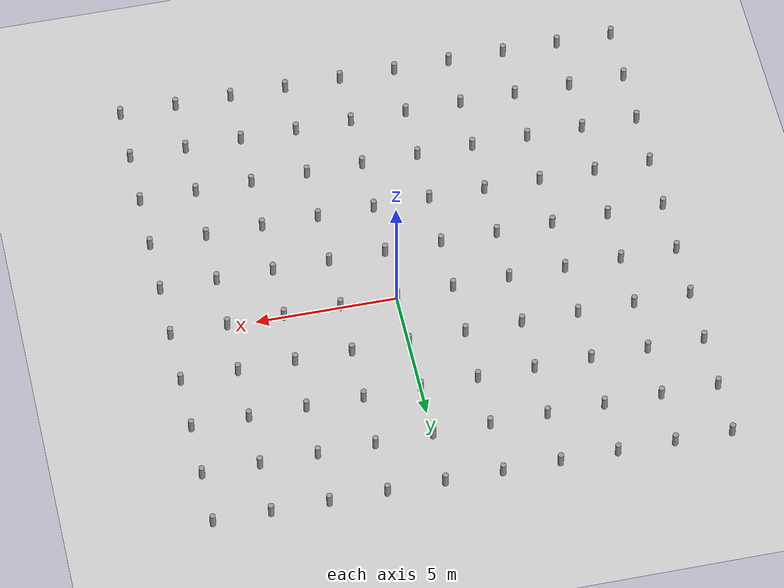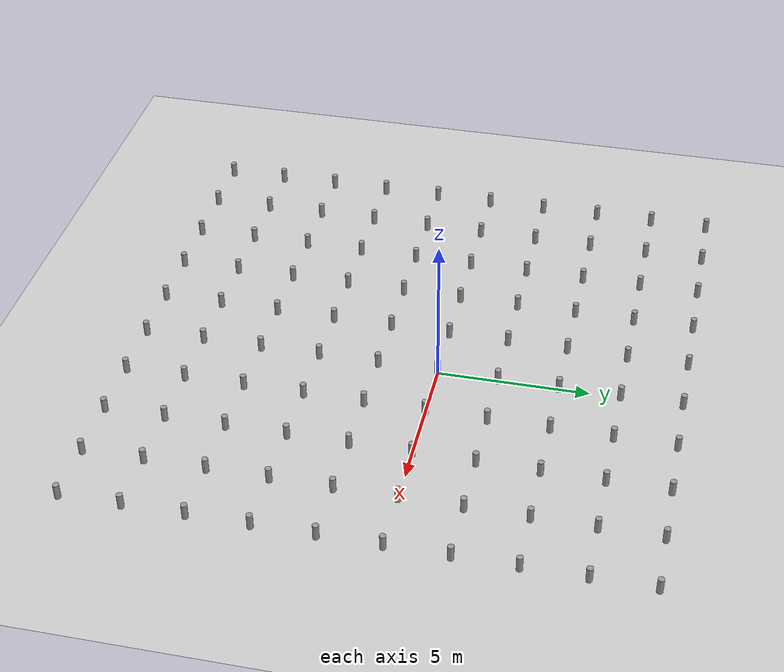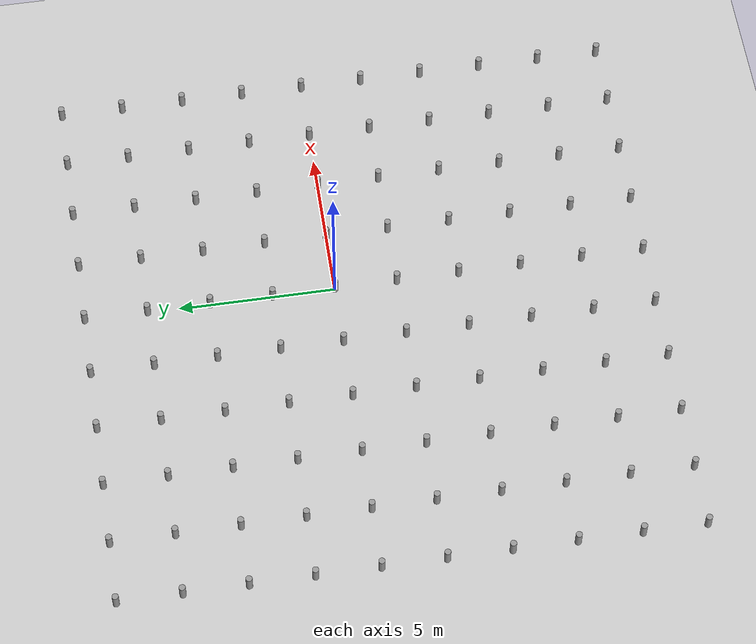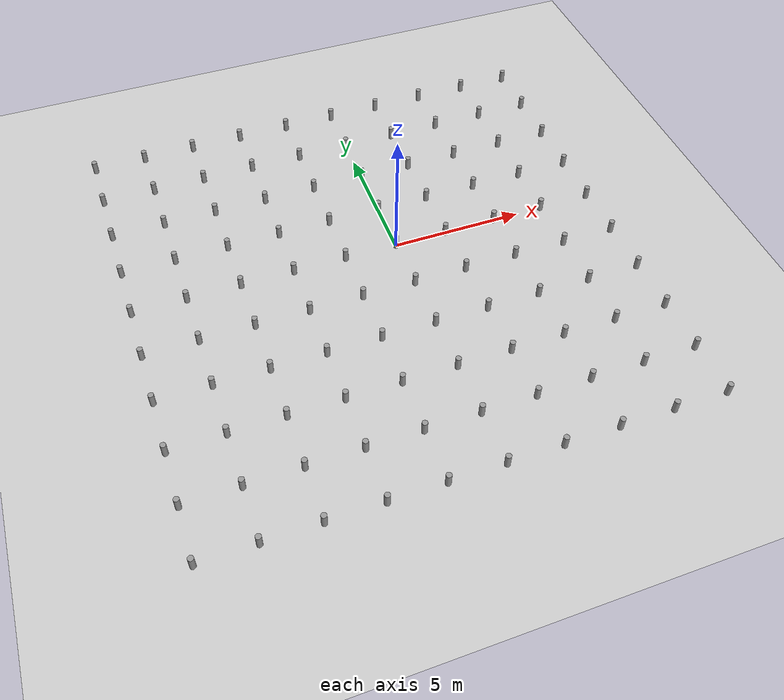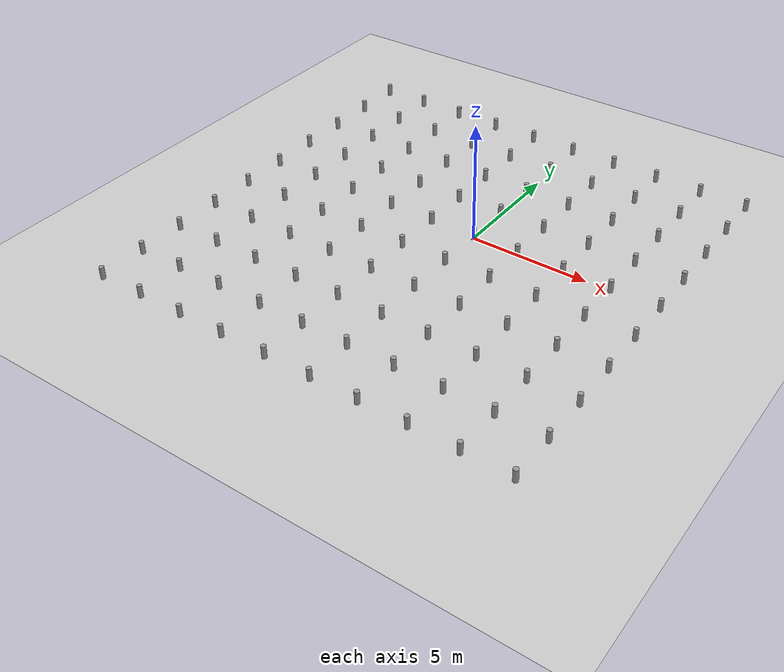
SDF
<sdf version="1.5">
 <world name="default">
  <light name="sun" type="directional">
   <pose>0 0 10 0 -0 0</pose>
   <diffuse>0.8 0.8 0.8 1</diffuse>
   <specular>0.2 0.2 0.2 1</specular>
   <attenuation>
    <range>1000</range>
    <constant>0.9</constant>
    <linear>0.01</linear>
    <quadratic>0.001</quadratic>
   </attenuation>
   <direction>-0.5 0.1 -0.9</direction>
  </light>
  <model name="ground_plane">
   <static>1</static>
   <link name="link">
    <collision name="collision">
     <geometry><plane><normal>0 0 1</normal><size>100 100</size></plane></geometry>
     <surface><friction><ode><mu>100</mu><mu2>50</mu2></ode></friction></surface>
    </collision>
    <visual name="visual">
     <cast_shadows>0</cast_shadows>
     <geometry><plane><normal>0 0 1</normal><size>100 100</size></plane></geometry>
     <material>
      <script><uri>file://media/materials/scripts/gazebo.material</uri><name>Gazebo/Grey</name></script>
     </material>
    </visual>
   </link>
  </model>
  <physics name="default_physics" default="0" type="ode">
   <max_step_size>0.001</max_step_size>
   <real_time_factor>1</real_time_factor>
   <real_time_update_rate>1000</real_time_update_rate>
   <gravity>0 0 -9.8</gravity>
   <magnetic_field>5.5645e-06 2.28758e-05 -4.23884e-05</magnetic_field>
  </physics>
  <scene><ambient>0.4 0.4 0.4 1</ambient><background>0.7 0.7 0.7 1</background><shadows>1</shadows></scene>
  <spherical_coordinates>
   <surface_model>EARTH_WGS84</surface_model>
   <latitude_deg>0</latitude_deg>
   <longitude_deg>0</longitude_deg>
   <elevation>0</elevation>
   <heading_deg>0</heading_deg>
  </spherical_coordinates>
  <model name="unit_cylinder_-10_-10">
   <pose>-10 -10 0 0 -0 1.7e-05</pose>
   <link name="link">
    <inertial>
     <mass>1</mass>
     <inertia><ixx>1</ixx><ixy>0</ixy><ixz>0</ixz><iyy>1</iyy><iyz>0</iyz><izz>1</izz></inertia>
    </inertial>
    <collision name="collision">
     <geometry><cylinder><radius>0.1</radius><length>1</length></cylinder></geometry>
    </collision>
    <visual name="visual">
     <geometry><cylinder><radius>0.1</radius><length>1</length></cylinder></geometry>
     <material>
      <script><uri>file://media/materials/scripts/gazebo.material</uri><name>Gazebo/Grey</name></script>
     </material>
    </visual>
   </link>
  </model>
  <model name="unit_cylinder_-10_-8">
   <pose>-10 -8 0 0 -0 1.7e-05</pose>
   <link name="link">
    <inertial>
     <mass>1</mass>
     <inertia><ixx>1</ixx><ixy>0</ixy><ixz>0</ixz><iyy>1</iyy><iyz>0</iyz><izz>1</izz></inertia>
    </inertial>
    <collision name="collision">
     <geometry><cylinder><radius>0.1</radius><length>1</length></cylinder></geometry>
    </collision>
    <visual name="visual">
     <geometry><cylinder><radius>0.1</radius><length>1</length></cylinder></geometry>
     <material>
      <script><uri>file://media/materials/scripts/gazebo.material</uri><name>Gazebo/Grey</name></script>
     </material>
    </visual>
   </link>
  </model>
  <model name="unit_cylinder_-10_-6">
   <pose>-10 -6 0 0 -0 1.7e-05</pose>
   <link name="link">
    <inertial>
     <mass>1</mass>
     <inertia><ixx>1</ixx><ixy>0</ixy><ixz>0</ixz><iyy>1</iyy><iyz>0</iyz><izz>1</izz></inertia>
    </inertial>
    <collision name="collision">
     <geometry><cylinder><radius>0.1</radius><length>1</length></cylinder></geometry>
    </collision>
    <visual name="visual">
     <geometry><cylinder><radius>0.1</radius><length>1</length></cylinder></geometry>
     <material>
      <script><uri>file://media/materials/scripts/gazebo.material</uri><name>Gazebo/Grey</name></script>
     </material>
    </visual>
   </link>
  </model>
  <model name="unit_cylinder_-10_-4">
   <pose>-10 -4 0 0 -0 1.7e-05</pose>
   <link name="link">
    <inertial>
     <mass>1</mass>
     <inertia><ixx>1</ixx><ixy>0</ixy><ixz>0</ixz><iyy>1</iyy><iyz>0</iyz><izz>1</izz></inertia>
    </inertial>
    <collision name="collision">
     <geometry><cylinder><radius>0.1</radius><length>1</length></cylinder></geometry>
    </collision>
    <visual name="visual">
     <geometry><cylinder><radius>0.1</radius><length>1</length></cylinder></geometry>
     <material>
      <script><uri>file://media/materials/scripts/gazebo.material</uri><name>Gazebo/Grey</name></script>
     </material>
    </visual>
   </link>
  </model>
  <model name="unit_cylinder_-10_-2">
   <pose>-10 -2 0 0 -0 1.7e-05</pose>
   <link name="link">
    <inertial>
     <mass>1</mass>
     <inertia><ixx>1</ixx><ixy>0</ixy><ixz>0</ixz><iyy>1</iyy><iyz>0</iyz><izz>1</izz></inertia>
    </inertial>
    <collision name="collision">
     <geometry><cylinder><radius>0.1</radius><length>1</length></cylinder></geometry>
    </collision>
    <visual name="visual">
     <geometry><cylinder><radius>0.1</radius><length>1</length></cylinder></geometry>
     <material>
      <script><uri>file://media/materials/scripts/gazebo.material</uri><name>Gazebo/Grey</name></script>
     </material>
    </visual>
   </link>
  </model>
  <model name="unit_cylinder_-10_0">
   <pose>-10 0 0 0 -0 1.7e-05</pose>
   <link name="link">
    <inertial>
     <mass>1</mass>
     <inertia><ixx>1</ixx><ixy>0</ixy><ixz>0</ixz><iyy>1</iyy><iyz>0</iyz><izz>1</izz></inertia>
    </inertial>
    <collision name="collision">
     <geometry><cylinder><radius>0.1</radius><length>1</length></cylinder></geometry>
    </collision>
    <visual name="visual">
     <geometry><cylinder><radius>0.1</radius><length>1</length></cylinder></geometry>
     <material>
      <script><uri>file://media/materials/scripts/gazebo.material</uri><name>Gazebo/Grey</name></script>
     </material>
    </visual>
   </link>
  </model>
  <model name="unit_cylinder_-10_2">
   <pose>-10 2 0 0 -0 1.7e-05</pose>
   <link name="link">
    <inertial>
     <mass>1</mass>
     <inertia><ixx>1</ixx><ixy>0</ixy><ixz>0</ixz><iyy>1</iyy><iyz>0</iyz><izz>1</izz></inertia>
    </inertial>
    <collision name="collision">
     <geometry><cylinder><radius>0.1</radius><length>1</length></cylinder></geometry>
    </collision>
    <visual name="visual">
     <geometry><cylinder><radius>0.1</radius><length>1</length></cylinder></geometry>
     <material>
      <script><uri>file://media/materials/scripts/gazebo.material</uri><name>Gazebo/Grey</name></script>
     </material>
    </visual>
   </link>
  </model>
  <model name="unit_cylinder_-10_4">
   <pose>-10 4 0 0 -0 1.7e-05</pose>
   <link name="link">
    <inertial>
     <mass>1</mass>
     <inertia><ixx>1</ixx><ixy>0</ixy><ixz>0</ixz><iyy>1</iyy><iyz>0</iyz><izz>1</izz></inertia>
    </inertial>
    <collision name="collision">
     <geometry><cylinder><radius>0.1</radius><length>1</length></cylinder></geometry>
    </collision>
    <visual name="visual">
     <geometry><cylinder><radius>0.1</radius><length>1</length></cylinder></geometry>
     <material>
      <script><uri>file://media/materials/scripts/gazebo.material</uri><name>Gazebo/Grey</name></script>
     </material>
    </visual>
   </link>
  </model>
  <model name="unit_cylinder_-10_6">
   <pose>-10 6 0 0 -0 1.7e-05</pose>
   <link name="link">
    <inertial>
     <mass>1</mass>
     <inertia><ixx>1</ixx><ixy>0</ixy><ixz>0</ixz><iyy>1</iyy><iyz>0</iyz><izz>1</izz></inertia>
    </inertial>
    <collision name="collision">
     <geometry><cylinder><radius>0.1</radius><length>1</length></cylinder></geometry>
    </collision>
    <visual name="visual">
     <geometry><cylinder><radius>0.1</radius><length>1</length></cylinder></geometry>
     <material>
      <script><uri>file://media/materials/scripts/gazebo.material</uri><name>Gazebo/Grey</name></script>
     </material>
    </visual>
   </link>
  </model>
  <model name="unit_cylinder_-10_8">
   <pose>-10 8 0 0 -0 1.7e-05</pose>
   <link name="link">
    <inertial>
     <mass>1</mass>
     <inertia><ixx>1</ixx><ixy>0</ixy><ixz>0</ixz><iyy>1</iyy><iyz>0</iyz><izz>1</izz></inertia>
    </inertial>
    <collision name="collision">
     <geometry><cylinder><radius>0.1</radius><length>1</length></cylinder></geometry>
    </collision>
    <visual name="visual">
     <geometry><cylinder><radius>0.1</radius><length>1</length></cylinder></geometry>
     <material>
      <script><uri>file://media/materials/scripts/gazebo.material</uri><name>Gazebo/Grey</name></script>
     </material>
    </visual>
   </link>
  </model>
  <model name="unit_cylinder_-8_-10">
   <pose>-8 -10 0 0 -0 1.7e-05</pose>
   <link name="link">
    <inertial>
     <mass>1</mass>
     <inertia><ixx>1</ixx><ixy>0</ixy><ixz>0</ixz><iyy>1</iyy><iyz>0</iyz><izz>1</izz></inertia>
    </inertial>
    <collision name="collision">
     <geometry><cylinder><radius>0.1</radius><length>1</length></cylinder></geometry>
    </collision>
    <visual name="visual">
     <geometry><cylinder><radius>0.1</radius><length>1</length></cylinder></geometry>
     <material>
      <script><uri>file://media/materials/scripts/gazebo.material</uri><name>Gazebo/Grey</name></script>
     </material>
    </visual>
   </link>
  </model>
  <model name="unit_cylinder_-8_-8">
   <pose>-8 -8 0 0 -0 1.7e-05</pose>
   <link name="link">
    <inertial>
     <mass>1</mass>
     <inertia><ixx>1</ixx><ixy>0</ixy><ixz>0</ixz><iyy>1</iyy><iyz>0</iyz><izz>1</izz></inertia>
    </inertial>
    <collision name="collision">
     <geometry><cylinder><radius>0.1</radius><length>1</length></cylinder></geometry>
    </collision>
    <visual name="visual">
     <geometry><cylinder><radius>0.1</radius><length>1</length></cylinder></geometry>
     <material>
      <script><uri>file://media/materials/scripts/gazebo.material</uri><name>Gazebo/Grey</name></script>
     </material>
    </visual>
   </link>
  </model>
  <model name="unit_cylinder_-8_-6">
   <pose>-8 -6 0 0 -0 1.7e-05</pose>
   <link name="link">
    <inertial>
     <mass>1</mass>
     <inertia><ixx>1</ixx><ixy>0</ixy><ixz>0</ixz><iyy>1</iyy><iyz>0</iyz><izz>1</izz></inertia>
    </inertial>
    <collision name="collision">
     <geometry><cylinder><radius>0.1</radius><length>1</length></cylinder></geometry>
    </collision>
    <visual name="visual">
     <geometry><cylinder><radius>0.1</radius><length>1</length></cylinder></geometry>
     <material>
      <script><uri>file://media/materials/scripts/gazebo.material</uri><name>Gazebo/Grey</name></script>
     </material>
    </visual>
   </link>
  </model>
  <model name="unit_cylinder_-8_-4">
   <pose>-8 -4 0 0 -0 1.7e-05</pose>
   <link name="link">
    <inertial>
     <mass>1</mass>
     <inertia><ixx>1</ixx><ixy>0</ixy><ixz>0</ixz><iyy>1</iyy><iyz>0</iyz><izz>1</izz></inertia>
    </inertial>
    <collision name="collision">
     <geometry><cylinder><radius>0.1</radius><length>1</length></cylinder></geometry>
    </collision>
    <visual name="visual">
     <geometry><cylinder><radius>0.1</radius><length>1</length></cylinder></geometry>
     <material>
      <script><uri>file://media/materials/scripts/gazebo.material</uri><name>Gazebo/Grey</name></script>
     </material>
    </visual>
   </link>
  </model>
  <model name="unit_cylinder_-8_-2">
   <pose>-8 -2 0 0 -0 1.7e-05</pose>
   <link name="link">
    <inertial>
     <mass>1</mass>
     <inertia><ixx>1</ixx><ixy>0</ixy><ixz>0</ixz><iyy>1</iyy><iyz>0</iyz><izz>1</izz></inertia>
    </inertial>
    <collision name="collision">
     <geometry><cylinder><radius>0.1</radius><length>1</length></cylinder></geometry>
    </collision>
    <visual name="visual">
     <geometry><cylinder><radius>0.1</radius><length>1</length></cylinder></geometry>
     <material>
      <script><uri>file://media/materials/scripts/gazebo.material</uri><name>Gazebo/Grey</name></script>
     </material>
    </visual>
   </link>
  </model>
  <model name="unit_cylinder_-8_0">
   <pose>-8 0 0 0 -0 1.7e-05</pose>
   <link name="link">
    <inertial>
     <mass>1</mass>
     <inertia><ixx>1</ixx><ixy>0</ixy><ixz>0</ixz><iyy>1</iyy><iyz>0</iyz><izz>1</izz></inertia>
    </inertial>
    <collision name="collision">
     <geometry><cylinder><radius>0.1</radius><length>1</length></cylinder></geometry>
    </collision>
    <visual name="visual">
     <geometry><cylinder><radius>0.1</radius><length>1</length></cylinder></geometry>
     <material>
      <script><uri>file://media/materials/scripts/gazebo.material</uri><name>Gazebo/Grey</name></script>
     </material>
    </visual>
   </link>
  </model>
  <model name="unit_cylinder_-8_2">
   <pose>-8 2 0 0 -0 1.7e-05</pose>
   <link name="link">
    <inertial>
     <mass>1</mass>
     <inertia><ixx>1</ixx><ixy>0</ixy><ixz>0</ixz><iyy>1</iyy><iyz>0</iyz><izz>1</izz></inertia>
    </inertial>
    <collision name="collision">
     <geometry><cylinder><radius>0.1</radius><length>1</length></cylinder></geometry>
    </collision>
    <visual name="visual">
     <geometry><cylinder><radius>0.1</radius><length>1</length></cylinder></geometry>
     <material>
      <script><uri>file://media/materials/scripts/gazebo.material</uri><name>Gazebo/Grey</name></script>
     </material>
    </visual>
   </link>
  </model>
  <model name="unit_cylinder_-8_4">
   <pose>-8 4 0 0 -0 1.7e-05</pose>
   <link name="link">
    <inertial>
     <mass>1</mass>
     <inertia><ixx>1</ixx><ixy>0</ixy><ixz>0</ixz><iyy>1</iyy><iyz>0</iyz><izz>1</izz></inertia>
    </inertial>
    <collision name="collision">
     <geometry><cylinder><radius>0.1</radius><length>1</length></cylinder></geometry>
    </collision>
    <visual name="visual">
     <geometry><cylinder><radius>0.1</radius><length>1</length></cylinder></geometry>
     <material>
      <script><uri>file://media/materials/scripts/gazebo.material</uri><name>Gazebo/Grey</name></script>
     </material>
    </visual>
   </link>
  </model>
  <model name="unit_cylinder_-8_6">
   <pose>-8 6 0 0 -0 1.7e-05</pose>
   <link name="link">
    <inertial>
     <mass>1</mass>
     <inertia><ixx>1</ixx><ixy>0</ixy><ixz>0</ixz><iyy>1</iyy><iyz>0</iyz><izz>1</izz></inertia>
    </inertial>
    <collision name="collision">
     <geometry><cylinder><radius>0.1</radius><length>1</length></cylinder></geometry>
    </collision>
    <visual name="visual">
     <geometry><cylinder><radius>0.1</radius><length>1</length></cylinder></geometry>
     <material>
      <script><uri>file://media/materials/scripts/gazebo.material</uri><name>Gazebo/Grey</name></script>
     </material>
    </visual>
   </link>
  </model>
  <model name="unit_cylinder_-8_8">
   <pose>-8 8 0 0 -0 1.7e-05</pose>
   <link name="link">
    <inertial>
     <mass>1</mass>
     <inertia><ixx>1</ixx><ixy>0</ixy><ixz>0</ixz><iyy>1</iyy><iyz>0</iyz><izz>1</izz></inertia>
    </inertial>
    <collision name="collision">
     <geometry><cylinder><radius>0.1</radius><length>1</length></cylinder></geometry>
    </collision>
    <visual name="visual">
     <geometry><cylinder><radius>0.1</radius><length>1</length></cylinder></geometry>
     <material>
      <script><uri>file://media/materials/scripts/gazebo.material</uri><name>Gazebo/Grey</name></script>
     </material>
    </visual>
   </link>
  </model>
  <model name="unit_cylinder_-6_-10">
   <pose>-6 -10 0 0 -0 1.7e-05</pose>
   <link name="link">
    <inertial>
     <mass>1</mass>
     <inertia><ixx>1</ixx><ixy>0</ixy><ixz>0</ixz><iyy>1</iyy><iyz>0</iyz><izz>1</izz></inertia>
    </inertial>
    <collision name="collision">
     <geometry><cylinder><radius>0.1</radius><length>1</length></cylinder></geometry>
    </collision>
    <visual name="visual">
     <geometry><cylinder><radius>0.1</radius><length>1</length></cylinder></geometry>
     <material>
      <script><uri>file://media/materials/scripts/gazebo.material</uri><name>Gazebo/Grey</name></script>
     </material>
    </visual>
   </link>
  </model>
  <model name="unit_cylinder_-6_-8">
   <pose>-6 -8 0 0 -0 1.7e-05</pose>
   <link name="link">
    <inertial>
     <mass>1</mass>
     <inertia><ixx>1</ixx><ixy>0</ixy><ixz>0</ixz><iyy>1</iyy><iyz>0</iyz><izz>1</izz></inertia>
    </inertial>
    <collision name="collision">
     <geometry><cylinder><radius>0.1</radius><length>1</length></cylinder></geometry>
    </collision>
    <visual name="visual">
     <geometry><cylinder><radius>0.1</radius><length>1</length></cylinder></geometry>
     <material>
      <script><uri>file://media/materials/scripts/gazebo.material</uri><name>Gazebo/Grey</name></script>
     </material>
    </visual>
   </link>
  </model>
  <model name="unit_cylinder_-6_-6">
   <pose>-6 -6 0 0 -0 1.7e-05</pose>
   <link name="link">
    <inertial>
     <mass>1</mass>
     <inertia><ixx>1</ixx><ixy>0</ixy><ixz>0</ixz><iyy>1</iyy><iyz>0</iyz><izz>1</izz></inertia>
    </inertial>
    <collision name="collision">
     <geometry><cylinder><radius>0.1</radius><length>1</length></cylinder></geometry>
    </collision>
    <visual name="visual">
     <geometry><cylinder><radius>0.1</radius><length>1</length></cylinder></geometry>
     <material>
      <script><uri>file://media/materials/scripts/gazebo.material</uri><name>Gazebo/Grey</name></script>
     </material>
    </visual>
   </link>
  </model>
  <model name="unit_cylinder_-6_-4">
   <pose>-6 -4 0 0 -0 1.7e-05</pose>
   <link name="link">
    <inertial>
     <mass>1</mass>
     <inertia><ixx>1</ixx><ixy>0</ixy><ixz>0</ixz><iyy>1</iyy><iyz>0</iyz><izz>1</izz></inertia>
    </inertial>
    <collision name="collision">
     <geometry><cylinder><radius>0.1</radius><length>1</length></cylinder></geometry>
    </collision>
    <visual name="visual">
     <geometry><cylinder><radius>0.1</radius><length>1</length></cylinder></geometry>
     <material>
      <script><uri>file://media/materials/scripts/gazebo.material</uri><name>Gazebo/Grey</name></script>
     </material>
    </visual>
   </link>
  </model>
  <model name="unit_cylinder_-6_-2">
   <pose>-6 -2 0 0 -0 1.7e-05</pose>
   <link name="link">
    <inertial>
     <mass>1</mass>
     <inertia><ixx>1</ixx><ixy>0</ixy><ixz>0</ixz><iyy>1</iyy><iyz>0</iyz><izz>1</izz></inertia>
    </inertial>
    <collision name="collision">
     <geometry><cylinder><radius>0.1</radius><length>1</length></cylinder></geometry>
    </collision>
    <visual name="visual">
     <geometry><cylinder><radius>0.1</radius><length>1</length></cylinder></geometry>
     <material>
      <script><uri>file://media/materials/scripts/gazebo.material</uri><name>Gazebo/Grey</name></script>
     </material>
    </visual>
   </link>
  </model>
  <model name="unit_cylinder_-6_0">
   <pose>-6 0 0 0 -0 1.7e-05</pose>
   <link name="link">
    <inertial>
     <mass>1</mass>
     <inertia><ixx>1</ixx><ixy>0</ixy><ixz>0</ixz><iyy>1</iyy><iyz>0</iyz><izz>1</izz></inertia>
    </inertial>
    <collision name="collision">
     <geometry><cylinder><radius>0.1</radius><length>1</length></cylinder></geometry>
    </collision>
    <visual name="visual">
     <geometry><cylinder><radius>0.1</radius><length>1</length></cylinder></geometry>
     <material>
      <script><uri>file://media/materials/scripts/gazebo.material</uri><name>Gazebo/Grey</name></script>
     </material>
    </visual>
   </link>
  </model>
  <model name="unit_cylinder_-6_2">
   <pose>-6 2 0 0 -0 1.7e-05</pose>
   <link name="link">
    <inertial>
     <mass>1</mass>
     <inertia><ixx>1</ixx><ixy>0</ixy><ixz>0</ixz><iyy>1</iyy><iyz>0</iyz><izz>1</izz></inertia>
    </inertial>
    <collision name="collision">
     <geometry><cylinder><radius>0.1</radius><length>1</length></cylinder></geometry>
    </collision>
    <visual name="visual">
     <geometry><cylinder><radius>0.1</radius><length>1</length></cylinder></geometry>
     <material>
      <script><uri>file://media/materials/scripts/gazebo.material</uri><name>Gazebo/Grey</name></script>
     </material>
    </visual>
   </link>
  </model>
  <model name="unit_cylinder_-6_4">
   <pose>-6 4 0 0 -0 1.7e-05</pose>
   <link name="link">
    <inertial>
     <mass>1</mass>
     <inertia><ixx>1</ixx><ixy>0</ixy><ixz>0</ixz><iyy>1</iyy><iyz>0</iyz><izz>1</izz></inertia>
    </inertial>
    <collision name="collision">
     <geometry><cylinder><radius>0.1</radius><length>1</length></cylinder></geometry>
    </collision>
    <visual name="visual">
     <geometry><cylinder><radius>0.1</radius><length>1</length></cylinder></geometry>
     <material>
      <script><uri>file://media/materials/scripts/gazebo.material</uri><name>Gazebo/Grey</name></script>
     </material>
    </visual>
   </link>
  </model>
  <model name="unit_cylinder_-6_6">
   <pose>-6 6 0 0 -0 1.7e-05</pose>
   <link name="link">
    <inertial>
     <mass>1</mass>
     <inertia><ixx>1</ixx><ixy>0</ixy><ixz>0</ixz><iyy>1</iyy><iyz>0</iyz><izz>1</izz></inertia>
    </inertial>
    <collision name="collision">
     <geometry><cylinder><radius>0.1</radius><length>1</length></cylinder></geometry>
    </collision>
    <visual name="visual">
     <geometry><cylinder><radius>0.1</radius><length>1</length></cylinder></geometry>
     <material>
      <script><uri>file://media/materials/scripts/gazebo.material</uri><name>Gazebo/Grey</name></script>
     </material>
    </visual>
   </link>
  </model>
  <model name="unit_cylinder_-6_8">
   <pose>-6 8 0 0 -0 1.7e-05</pose>
   <link name="link">
    <inertial>
     <mass>1</mass>
     <inertia><ixx>1</ixx><ixy>0</ixy><ixz>0</ixz><iyy>1</iyy><iyz>0</iyz><izz>1</izz></inertia>
    </inertial>
    <collision name="collision">
     <geometry><cylinder><radius>0.1</radius><length>1</length></cylinder></geometry>
    </collision>
    <visual name="visual">
     <geometry><cylinder><radius>0.1</radius><length>1</length></cylinder></geometry>
     <material>
      <script><uri>file://media/materials/scripts/gazebo.material</uri><name>Gazebo/Grey</name></script>
     </material>
    </visual>
   </link>
  </model>
  <model name="unit_cylinder_-4_-10">
   <pose>-4 -10 0 0 -0 1.7e-05</pose>
   <link name="link">
    <inertial>
     <mass>1</mass>
     <inertia><ixx>1</ixx><ixy>0</ixy><ixz>0</ixz><iyy>1</iyy><iyz>0</iyz><izz>1</izz></inertia>
    </inertial>
    <collision name="collision">
     <geometry><cylinder><radius>0.1</radius><length>1</length></cylinder></geometry>
    </collision>
    <visual name="visual">
     <geometry><cylinder><radius>0.1</radius><length>1</length></cylinder></geometry>
     <material>
      <script><uri>file://media/materials/scripts/gazebo.material</uri><name>Gazebo/Grey</name></script>
     </material>
    </visual>
   </link>
  </model>
  <model name="unit_cylinder_-4_-8">
   <pose>-4 -8 0 0 -0 1.7e-05</pose>
   <link name="link">
    <inertial>
     <mass>1</mass>
     <inertia><ixx>1</ixx><ixy>0</ixy><ixz>0</ixz><iyy>1</iyy><iyz>0</iyz><izz>1</izz></inertia>
    </inertial>
    <collision name="collision">
     <geometry><cylinder><radius>0.1</radius><length>1</length></cylinder></geometry>
    </collision>
    <visual name="visual">
     <geometry><cylinder><radius>0.1</radius><length>1</length></cylinder></geometry>
     <material>
      <script><uri>file://media/materials/scripts/gazebo.material</uri><name>Gazebo/Grey</name></script>
     </material>
    </visual>
   </link>
  </model>
  <model name="unit_cylinder_-4_-6">
   <pose>-4 -6 0 0 -0 1.7e-05</pose>
   <link name="link">
    <inertial>
     <mass>1</mass>
     <inertia><ixx>1</ixx><ixy>0</ixy><ixz>0</ixz><iyy>1</iyy><iyz>0</iyz><izz>1</izz></inertia>
    </inertial>
    <collision name="collision">
     <geometry><cylinder><radius>0.1</radius><length>1</length></cylinder></geometry>
    </collision>
    <visual name="visual">
     <geometry><cylinder><radius>0.1</radius><length>1</length></cylinder></geometry>
     <material>
      <script><uri>file://media/materials/scripts/gazebo.material</uri><name>Gazebo/Grey</name></script>
     </material>
    </visual>
   </link>
  </model>
  <model name="unit_cylinder_-4_-4">
   <pose>-4 -4 0 0 -0 1.7e-05</pose>
   <link name="link">
    <inertial>
     <mass>1</mass>
     <inertia><ixx>1</ixx><ixy>0</ixy><ixz>0</ixz><iyy>1</iyy><iyz>0</iyz><izz>1</izz></inertia>
    </inertial>
    <collision name="collision">
     <geometry><cylinder><radius>0.1</radius><length>1</length></cylinder></geometry>
    </collision>
    <visual name="visual">
     <geometry><cylinder><radius>0.1</radius><length>1</length></cylinder></geometry>
     <material>
      <script><uri>file://media/materials/scripts/gazebo.material</uri><name>Gazebo/Grey</name></script>
     </material>
    </visual>
   </link>
  </model>
  <model name="unit_cylinder_-4_-2">
   <pose>-4 -2 0 0 -0 1.7e-05</pose>
   <link name="link">
    <inertial>
     <mass>1</mass>
     <inertia><ixx>1</ixx><ixy>0</ixy><ixz>0</ixz><iyy>1</iyy><iyz>0</iyz><izz>1</izz></inertia>
    </inertial>
    <collision name="collision">
     <geometry><cylinder><radius>0.1</radius><length>1</length></cylinder></geometry>
    </collision>
    <visual name="visual">
     <geometry><cylinder><radius>0.1</radius><length>1</length></cylinder></geometry>
     <material>
      <script><uri>file://media/materials/scripts/gazebo.material</uri><name>Gazebo/Grey</name></script>
     </material>
    </visual>
   </link>
  </model>
  <model name="unit_cylinder_-4_0">
   <pose>-4 0 0 0 -0 1.7e-05</pose>
   <link name="link">
    <inertial>
     <mass>1</mass>
     <inertia><ixx>1</ixx><ixy>0</ixy><ixz>0</ixz><iyy>1</iyy><iyz>0</iyz><izz>1</izz></inertia>
    </inertial>
    <collision name="collision">
     <geometry><cylinder><radius>0.1</radius><length>1</length></cylinder></geometry>
    </collision>
    <visual name="visual">
     <geometry><cylinder><radius>0.1</radius><length>1</length></cylinder></geometry>
     <material>
      <script><uri>file://media/materials/scripts/gazebo.material</uri><name>Gazebo/Grey</name></script>
     </material>
    </visual>
   </link>
  </model>
  <model name="unit_cylinder_-4_2">
   <pose>-4 2 0 0 -0 1.7e-05</pose>
   <link name="link">
    <inertial>
     <mass>1</mass>
     <inertia><ixx>1</ixx><ixy>0</ixy><ixz>0</ixz><iyy>1</iyy><iyz>0</iyz><izz>1</izz></inertia>
    </inertial>
    <collision name="collision">
     <geometry><cylinder><radius>0.1</radius><length>1</length></cylinder></geometry>
    </collision>
    <visual name="visual">
     <geometry><cylinder><radius>0.1</radius><length>1</length></cylinder></geometry>
     <material>
      <script><uri>file://media/materials/scripts/gazebo.material</uri><name>Gazebo/Grey</name></script>
     </material>
    </visual>
   </link>
  </model>
  <model name="unit_cylinder_-4_4">
   <pose>-4 4 0 0 -0 1.7e-05</pose>
   <link name="link">
    <inertial>
     <mass>1</mass>
     <inertia><ixx>1</ixx><ixy>0</ixy><ixz>0</ixz><iyy>1</iyy><iyz>0</iyz><izz>1</izz></inertia>
    </inertial>
    <collision name="collision">
     <geometry><cylinder><radius>0.1</radius><length>1</length></cylinder></geometry>
    </collision>
    <visual name="visual">
     <geometry><cylinder><radius>0.1</radius><length>1</length></cylinder></geometry>
     <material>
      <script><uri>file://media/materials/scripts/gazebo.material</uri><name>Gazebo/Grey</name></script>
     </material>
    </visual>
   </link>
  </model>
  <model name="unit_cylinder_-4_6">
   <pose>-4 6 0 0 -0 1.7e-05</pose>
   <link name="link">
    <inertial>
     <mass>1</mass>
     <inertia><ixx>1</ixx><ixy>0</ixy><ixz>0</ixz><iyy>1</iyy><iyz>0</iyz><izz>1</izz></inertia>
    </inertial>
    <collision name="collision">
     <geometry><cylinder><radius>0.1</radius><length>1</length></cylinder></geometry>
    </collision>
    <visual name="visual">
     <geometry><cylinder><radius>0.1</radius><length>1</length></cylinder></geometry>
     <material>
      <script><uri>file://media/materials/scripts/gazebo.material</uri><name>Gazebo/Grey</name></script>
     </material>
    </visual>
   </link>
  </model>
  <model name="unit_cylinder_-4_8">
   <pose>-4 8 0 0 -0 1.7e-05</pose>
   <link name="link">
    <inertial>
     <mass>1</mass>
     <inertia><ixx>1</ixx><ixy>0</ixy><ixz>0</ixz><iyy>1</iyy><iyz>0</iyz><izz>1</izz></inertia>
    </inertial>
    <collision name="collision">
     <geometry><cylinder><radius>0.1</radius><length>1</length></cylinder></geometry>
    </collision>
    <visual name="visual">
     <geometry><cylinder><radius>0.1</radius><length>1</length></cylinder></geometry>
     <material>
      <script><uri>file://media/materials/scripts/gazebo.material</uri><name>Gazebo/Grey</name></script>
     </material>
    </visual>
   </link>
  </model>
  <model name="unit_cylinder_-2_-10">
   <pose>-2 -10 0 0 -0 1.7e-05</pose>
   <link name="link">
    <inertial>
     <mass>1</mass>
     <inertia><ixx>1</ixx><ixy>0</ixy><ixz>0</ixz><iyy>1</iyy><iyz>0</iyz><izz>1</izz></inertia>
    </inertial>
    <collision name="collision">
     <geometry><cylinder><radius>0.1</radius><length>1</length></cylinder></geometry>
    </collision>
    <visual name="visual">
     <geometry><cylinder><radius>0.1</radius><length>1</length></cylinder></geometry>
     <material>
      <script><uri>file://media/materials/scripts/gazebo.material</uri><name>Gazebo/Grey</name></script>
     </material>
    </visual>
   </link>
  </model>
  <model name="unit_cylinder_-2_-8">
   <pose>-2 -8 0 0 -0 1.7e-05</pose>
   <link name="link">
    <inertial>
     <mass>1</mass>
     <inertia><ixx>1</ixx><ixy>0</ixy><ixz>0</ixz><iyy>1</iyy><iyz>0</iyz><izz>1</izz></inertia>
    </inertial>
    <collision name="collision">
     <geometry><cylinder><radius>0.1</radius><length>1</length></cylinder></geometry>
    </collision>
    <visual name="visual">
     <geometry><cylinder><radius>0.1</radius><length>1</length></cylinder></geometry>
     <material>
      <script><uri>file://media/materials/scripts/gazebo.material</uri><name>Gazebo/Grey</name></script>
     </material>
    </visual>
   </link>
  </model>
  <model name="unit_cylinder_-2_-6">
   <pose>-2 -6 0 0 -0 1.7e-05</pose>
   <link name="link">
    <inertial>
     <mass>1</mass>
     <inertia><ixx>1</ixx><ixy>0</ixy><ixz>0</ixz><iyy>1</iyy><iyz>0</iyz><izz>1</izz></inertia>
    </inertial>
    <collision name="collision">
     <geometry><cylinder><radius>0.1</radius><length>1</length></cylinder></geometry>
    </collision>
    <visual name="visual">
     <geometry><cylinder><radius>0.1</radius><length>1</length></cylinder></geometry>
     <material>
      <script><uri>file://media/materials/scripts/gazebo.material</uri><name>Gazebo/Grey</name></script>
     </material>
    </visual>
   </link>
  </model>
  <model name="unit_cylinder_-2_-4">
   <pose>-2 -4 0 0 -0 1.7e-05</pose>
   <link name="link">
    <inertial>
     <mass>1</mass>
     <inertia><ixx>1</ixx><ixy>0</ixy><ixz>0</ixz><iyy>1</iyy><iyz>0</iyz><izz>1</izz></inertia>
    </inertial>
    <collision name="collision">
     <geometry><cylinder><radius>0.1</radius><length>1</length></cylinder></geometry>
    </collision>
    <visual name="visual">
     <geometry><cylinder><radius>0.1</radius><length>1</length></cylinder></geometry>
     <material>
      <script><uri>file://media/materials/scripts/gazebo.material</uri><name>Gazebo/Grey</name></script>
     </material>
    </visual>
   </link>
  </model>
  <model name="unit_cylinder_-2_-2">
   <pose>-2 -2 0 0 -0 1.7e-05</pose>
   <link name="link">
    <inertial>
     <mass>1</mass>
     <inertia><ixx>1</ixx><ixy>0</ixy><ixz>0</ixz><iyy>1</iyy><iyz>0</iyz><izz>1</izz></inertia>
    </inertial>
    <collision name="collision">
     <geometry><cylinder><radius>0.1</radius><length>1</length></cylinder></geometry>
    </collision>
    <visual name="visual">
     <geometry><cylinder><radius>0.1</radius><length>1</length></cylinder></geometry>
     <material>
      <script><uri>file://media/materials/scripts/gazebo.material</uri><name>Gazebo/Grey</name></script>
     </material>
    </visual>
   </link>
  </model>
  <model name="unit_cylinder_-2_0">
   <pose>-2 0 0 0 -0 1.7e-05</pose>
   <link name="link">
    <inertial>
     <mass>1</mass>
     <inertia><ixx>1</ixx><ixy>0</ixy><ixz>0</ixz><iyy>1</iyy><iyz>0</iyz><izz>1</izz></inertia>
    </inertial>
    <collision name="collision">
     <geometry><cylinder><radius>0.1</radius><length>1</length></cylinder></geometry>
    </collision>
    <visual name="visual">
     <geometry><cylinder><radius>0.1</radius><length>1</length></cylinder></geometry>
     <material>
      <script><uri>file://media/materials/scripts/gazebo.material</uri><name>Gazebo/Grey</name></script>
     </material>
    </visual>
   </link>
  </model>
  <model name="unit_cylinder_-2_2">
   <pose>-2 2 0 0 -0 1.7e-05</pose>
   <link name="link">
    <inertial>
     <mass>1</mass>
     <inertia><ixx>1</ixx><ixy>0</ixy><ixz>0</ixz><iyy>1</iyy><iyz>0</iyz><izz>1</izz></inertia>
    </inertial>
    <collision name="collision">
     <geometry><cylinder><radius>0.1</radius><length>1</length></cylinder></geometry>
    </collision>
    <visual name="visual">
     <geometry><cylinder><radius>0.1</radius><length>1</length></cylinder></geometry>
     <material>
      <script><uri>file://media/materials/scripts/gazebo.material</uri><name>Gazebo/Grey</name></script>
     </material>
    </visual>
   </link>
  </model>
  <model name="unit_cylinder_-2_4">
   <pose>-2 4 0 0 -0 1.7e-05</pose>
   <link name="link">
    <inertial>
     <mass>1</mass>
     <inertia><ixx>1</ixx><ixy>0</ixy><ixz>0</ixz><iyy>1</iyy><iyz>0</iyz><izz>1</izz></inertia>
    </inertial>
    <collision name="collision">
     <geometry><cylinder><radius>0.1</radius><length>1</length></cylinder></geometry>
    </collision>
    <visual name="visual">
     <geometry><cylinder><radius>0.1</radius><length>1</length></cylinder></geometry>
     <material>
      <script><uri>file://media/materials/scripts/gazebo.material</uri><name>Gazebo/Grey</name></script>
     </material>
    </visual>
   </link>
  </model>
  <model name="unit_cylinder_-2_6">
   <pose>-2 6 0 0 -0 1.7e-05</pose>
   <link name="link">
    <inertial>
     <mass>1</mass>
     <inertia><ixx>1</ixx><ixy>0</ixy><ixz>0</ixz><iyy>1</iyy><iyz>0</iyz><izz>1</izz></inertia>
    </inertial>
    <collision name="collision">
     <geometry><cylinder><radius>0.1</radius><length>1</length></cylinder></geometry>
    </collision>
    <visual name="visual">
     <geometry><cylinder><radius>0.1</radius><length>1</length></cylinder></geometry>
     <material>
      <script><uri>file://media/materials/scripts/gazebo.material</uri><name>Gazebo/Grey</name></script>
     </material>
    </visual>
   </link>
  </model>
  <model name="unit_cylinder_-2_8">
   <pose>-2 8 0 0 -0 1.7e-05</pose>
   <link name="link">
    <inertial>
     <mass>1</mass>
     <inertia><ixx>1</ixx><ixy>0</ixy><ixz>0</ixz><iyy>1</iyy><iyz>0</iyz><izz>1</izz></inertia>
    </inertial>
    <collision name="collision">
     <geometry><cylinder><radius>0.1</radius><length>1</length></cylinder></geometry>
    </collision>
    <visual name="visual">
     <geometry><cylinder><radius>0.1</radius><length>1</length></cylinder></geometry>
     <material>
      <script><uri>file://media/materials/scripts/gazebo.material</uri><name>Gazebo/Grey</name></script>
     </material>
    </visual>
   </link>
  </model>
  <model name="unit_cylinder_0_-10">
   <pose>0 -10 0 0 -0 1.7e-05</pose>
   <link name="link">
    <inertial>
     <mass>1</mass>
     <inertia><ixx>1</ixx><ixy>0</ixy><ixz>0</ixz><iyy>1</iyy><iyz>0</iyz><izz>1</izz></inertia>
    </inertial>
    <collision name="collision">
     <geometry><cylinder><radius>0.1</radius><length>1</length></cylinder></geometry>
    </collision>
    <visual name="visual">
     <geometry><cylinder><radius>0.1</radius><length>1</length></cylinder></geometry>
     <material>
      <script><uri>file://media/materials/scripts/gazebo.material</uri><name>Gazebo/Grey</name></script>
     </material>
    </visual>
   </link>
  </model>
  <model name="unit_cylinder_0_-8">
   <pose>0 -8 0 0 -0 1.7e-05</pose>
   <link name="link">
    <inertial>
     <mass>1</mass>
     <inertia><ixx>1</ixx><ixy>0</ixy><ixz>0</ixz><iyy>1</iyy><iyz>0</iyz><izz>1</izz></inertia>
    </inertial>
    <collision name="collision">
     <geometry><cylinder><radius>0.1</radius><length>1</length></cylinder></geometry>
    </collision>
    <visual name="visual">
     <geometry><cylinder><radius>0.1</radius><length>1</length></cylinder></geometry>
     <material>
      <script><uri>file://media/materials/scripts/gazebo.material</uri><name>Gazebo/Grey</name></script>
     </material>
    </visual>
   </link>
  </model>
  <model name="unit_cylinder_0_-6">
   <pose>0 -6 0 0 -0 1.7e-05</pose>
   <link name="link">
    <inertial>
     <mass>1</mass>
     <inertia><ixx>1</ixx><ixy>0</ixy><ixz>0</ixz><iyy>1</iyy><iyz>0</iyz><izz>1</izz></inertia>
    </inertial>
    <collision name="collision">
     <geometry><cylinder><radius>0.1</radius><length>1</length></cylinder></geometry>
    </collision>
    <visual name="visual">
     <geometry><cylinder><radius>0.1</radius><length>1</length></cylinder></geometry>
     <material>
      <script><uri>file://media/materials/scripts/gazebo.material</uri><name>Gazebo/Grey</name></script>
     </material>
    </visual>
   </link>
  </model>
  <model name="unit_cylinder_0_-4">
   <pose>0 -4 0 0 -0 1.7e-05</pose>
   <link name="link">
    <inertial>
     <mass>1</mass>
     <inertia><ixx>1</ixx><ixy>0</ixy><ixz>0</ixz><iyy>1</iyy><iyz>0</iyz><izz>1</izz></inertia>
    </inertial>
    <collision name="collision">
     <geometry><cylinder><radius>0.1</radius><length>1</length></cylinder></geometry>
    </collision>
    <visual name="visual">
     <geometry><cylinder><radius>0.1</radius><length>1</length></cylinder></geometry>
     <material>
      <script><uri>file://media/materials/scripts/gazebo.material</uri><name>Gazebo/Grey</name></script>
     </material>
    </visual>
   </link>
  </model>
  <model name="unit_cylinder_0_-2">
   <pose>0 -2 0 0 -0 1.7e-05</pose>
   <link name="link">
    <inertial>
     <mass>1</mass>
     <inertia><ixx>1</ixx><ixy>0</ixy><ixz>0</ixz><iyy>1</iyy><iyz>0</iyz><izz>1</izz></inertia>
    </inertial>
    <collision name="collision">
     <geometry><cylinder><radius>0.1</radius><length>1</length></cylinder></geometry>
    </collision>
    <visual name="visual">
     <geometry><cylinder><radius>0.1</radius><length>1</length></cylinder></geometry>
     <material>
      <script><uri>file://media/materials/scripts/gazebo.material</uri><name>Gazebo/Grey</name></script>
     </material>
    </visual>
   </link>
  </model>
  <model name="unit_cylinder_0_0">
   <pose>0 0 0 0 -0 1.7e-05</pose>
   <link name="link">
    <inertial>
     <mass>1</mass>
     <inertia><ixx>1</ixx><ixy>0</ixy><ixz>0</ixz><iyy>1</iyy><iyz>0</iyz><izz>1</izz></inertia>
    </inertial>
    <collision name="collision">
     <geometry><cylinder><radius>0.1</radius><length>1</length></cylinder></geometry>
    </collision>
    <visual name="visual">
     <geometry><cylinder><radius>0.1</radius><length>1</length></cylinder></geometry>
     <material>
      <script><uri>file://media/materials/scripts/gazebo.material</uri><name>Gazebo/Grey</name></script>
     </material>
    </visual>
   </link>
  </model>
  <model name="unit_cylinder_0_2">
   <pose>0 2 0 0 -0 1.7e-05</pose>
   <link name="link">
    <inertial>
     <mass>1</mass>
     <inertia><ixx>1</ixx><ixy>0</ixy><ixz>0</ixz><iyy>1</iyy><iyz>0</iyz><izz>1</izz></inertia>
    </inertial>
    <collision name="collision">
     <geometry><cylinder><radius>0.1</radius><length>1</length></cylinder></geometry>
    </collision>
    <visual name="visual">
     <geometry><cylinder><radius>0.1</radius><length>1</length></cylinder></geometry>
     <material>
      <script><uri>file://media/materials/scripts/gazebo.material</uri><name>Gazebo/Grey</name></script>
     </material>
    </visual>
   </link>
  </model>
  <model name="unit_cylinder_0_4">
   <pose>0 4 0 0 -0 1.7e-05</pose>
   <link name="link">
    <inertial>
     <mass>1</mass>
     <inertia><ixx>1</ixx><ixy>0</ixy><ixz>0</ixz><iyy>1</iyy><iyz>0</iyz><izz>1</izz></inertia>
    </inertial>
    <collision name="collision">
     <geometry><cylinder><radius>0.1</radius><length>1</length></cylinder></geometry>
    </collision>
    <visual name="visual">
     <geometry><cylinder><radius>0.1</radius><length>1</length></cylinder></geometry>
     <material>
      <script><uri>file://media/materials/scripts/gazebo.material</uri><name>Gazebo/Grey</name></script>
     </material>
    </visual>
   </link>
  </model>
  <model name="unit_cylinder_0_6">
   <pose>0 6 0 0 -0 1.7e-05</pose>
   <link name="link">
    <inertial>
     <mass>1</mass>
     <inertia><ixx>1</ixx><ixy>0</ixy><ixz>0</ixz><iyy>1</iyy><iyz>0</iyz><izz>1</izz></inertia>
    </inertial>
    <collision name="collision">
     <geometry><cylinder><radius>0.1</radius><length>1</length></cylinder></geometry>
    </collision>
    <visual name="visual">
     <geometry><cylinder><radius>0.1</radius><length>1</length></cylinder></geometry>
     <material>
      <script><uri>file://media/materials/scripts/gazebo.material</uri><name>Gazebo/Grey</name></script>
     </material>
    </visual>
   </link>
  </model>
  <model name="unit_cylinder_0_8">
   <pose>0 8 0 0 -0 1.7e-05</pose>
   <link name="link">
    <inertial>
     <mass>1</mass>
     <inertia><ixx>1</ixx><ixy>0</ixy><ixz>0</ixz><iyy>1</iyy><iyz>0</iyz><izz>1</izz></inertia>
    </inertial>
    <collision name="collision">
     <geometry><cylinder><radius>0.1</radius><length>1</length></cylinder></geometry>
    </collision>
    <visual name="visual">
     <geometry><cylinder><radius>0.1</radius><length>1</length></cylinder></geometry>
     <material>
      <script><uri>file://media/materials/scripts/gazebo.material</uri><name>Gazebo/Grey</name></script>
     </material>
    </visual>
   </link>
  </model>
  <model name="unit_cylinder_2_-10">
   <pose>2 -10 0 0 -0 1.7e-05</pose>
   <link name="link">
    <inertial>
     <mass>1</mass>
     <inertia><ixx>1</ixx><ixy>0</ixy><ixz>0</ixz><iyy>1</iyy><iyz>0</iyz><izz>1</izz></inertia>
    </inertial>
    <collision name="collision">
     <geometry><cylinder><radius>0.1</radius><length>1</length></cylinder></geometry>
    </collision>
    <visual name="visual">
     <geometry><cylinder><radius>0.1</radius><length>1</length></cylinder></geometry>
     <material>
      <script><uri>file://media/materials/scripts/gazebo.material</uri><name>Gazebo/Grey</name></script>
     </material>
    </visual>
   </link>
  </model>
  <model name="unit_cylinder_2_-8">
   <pose>2 -8 0 0 -0 1.7e-05</pose>
   <link name="link">
    <inertial>
     <mass>1</mass>
     <inertia><ixx>1</ixx><ixy>0</ixy><ixz>0</ixz><iyy>1</iyy><iyz>0</iyz><izz>1</izz></inertia>
    </inertial>
    <collision name="collision">
     <geometry><cylinder><radius>0.1</radius><length>1</length></cylinder></geometry>
    </collision>
    <visual name="visual">
     <geometry><cylinder><radius>0.1</radius><length>1</length></cylinder></geometry>
     <material>
      <script><uri>file://media/materials/scripts/gazebo.material</uri><name>Gazebo/Grey</name></script>
     </material>
    </visual>
   </link>
  </model>
  <model name="unit_cylinder_2_-6">
   <pose>2 -6 0 0 -0 1.7e-05</pose>
   <link name="link">
    <inertial>
     <mass>1</mass>
     <inertia><ixx>1</ixx><ixy>0</ixy><ixz>0</ixz><iyy>1</iyy><iyz>0</iyz><izz>1</izz></inertia>
    </inertial>
    <collision name="collision">
     <geometry><cylinder><radius>0.1</radius><length>1</length></cylinder></geometry>
    </collision>
    <visual name="visual">
     <geometry><cylinder><radius>0.1</radius><length>1</length></cylinder></geometry>
     <material>
      <script><uri>file://media/materials/scripts/gazebo.material</uri><name>Gazebo/Grey</name></script>
     </material>
    </visual>
   </link>
  </model>
  <model name="unit_cylinder_2_-4">
   <pose>2 -4 0 0 -0 1.7e-05</pose>
   <link name="link">
    <inertial>
     <mass>1</mass>
     <inertia><ixx>1</ixx><ixy>0</ixy><ixz>0</ixz><iyy>1</iyy><iyz>0</iyz><izz>1</izz></inertia>
    </inertial>
    <collision name="collision">
     <geometry><cylinder><radius>0.1</radius><length>1</length></cylinder></geometry>
    </collision>
    <visual name="visual">
     <geometry><cylinder><radius>0.1</radius><length>1</length></cylinder></geometry>
     <material>
      <script><uri>file://media/materials/scripts/gazebo.material</uri><name>Gazebo/Grey</name></script>
     </material>
    </visual>
   </link>
  </model>
  <model name="unit_cylinder_2_-2">
   <pose>2 -2 0 0 -0 1.7e-05</pose>
   <link name="link">
    <inertial>
     <mass>1</mass>
     <inertia><ixx>1</ixx><ixy>0</ixy><ixz>0</ixz><iyy>1</iyy><iyz>0</iyz><izz>1</izz></inertia>
    </inertial>
    <collision name="collision">
     <geometry><cylinder><radius>0.1</radius><length>1</length></cylinder></geometry>
    </collision>
    <visual name="visual">
     <geometry><cylinder><radius>0.1</radius><length>1</length></cylinder></geometry>
     <material>
      <script><uri>file://media/materials/scripts/gazebo.material</uri><name>Gazebo/Grey</name></script>
     </material>
    </visual>
   </link>
  </model>
  <model name="unit_cylinder_2_0">
   <pose>2 0 0 0 -0 1.7e-05</pose>
   <link name="link">
    <inertial>
     <mass>1</mass>
     <inertia><ixx>1</ixx><ixy>0</ixy><ixz>0</ixz><iyy>1</iyy><iyz>0</iyz><izz>1</izz></inertia>
    </inertial>
    <collision name="collision">
     <geometry><cylinder><radius>0.1</radius><length>1</length></cylinder></geometry>
    </collision>
    <visual name="visual">
     <geometry><cylinder><radius>0.1</radius><length>1</length></cylinder></geometry>
     <material>
      <script><uri>file://media/materials/scripts/gazebo.material</uri><name>Gazebo/Grey</name></script>
     </material>
    </visual>
   </link>
  </model>
  <model name="unit_cylinder_2_2">
   <pose>2 2 0 0 -0 1.7e-05</pose>
   <link name="link">
    <inertial>
     <mass>1</mass>
     <inertia><ixx>1</ixx><ixy>0</ixy><ixz>0</ixz><iyy>1</iyy><iyz>0</iyz><izz>1</izz></inertia>
    </inertial>
    <collision name="collision">
     <geometry><cylinder><radius>0.1</radius><length>1</length></cylinder></geometry>
    </collision>
    <visual name="visual">
     <geometry><cylinder><radius>0.1</radius><length>1</length></cylinder></geometry>
     <material>
      <script><uri>file://media/materials/scripts/gazebo.material</uri><name>Gazebo/Grey</name></script>
     </material>
    </visual>
   </link>
  </model>
  <model name="unit_cylinder_2_4">
   <pose>2 4 0 0 -0 1.7e-05</pose>
   <link name="link">
    <inertial>
     <mass>1</mass>
     <inertia><ixx>1</ixx><ixy>0</ixy><ixz>0</ixz><iyy>1</iyy><iyz>0</iyz><izz>1</izz></inertia>
    </inertial>
    <collision name="collision">
     <geometry><cylinder><radius>0.1</radius><length>1</length></cylinder></geometry>
    </collision>
    <visual name="visual">
     <geometry><cylinder><radius>0.1</radius><length>1</length></cylinder></geometry>
     <material>
      <script><uri>file://media/materials/scripts/gazebo.material</uri><name>Gazebo/Grey</name></script>
     </material>
    </visual>
   </link>
  </model>
  <model name="unit_cylinder_2_6">
   <pose>2 6 0 0 -0 1.7e-05</pose>
   <link name="link">
    <inertial>
     <mass>1</mass>
     <inertia><ixx>1</ixx><ixy>0</ixy><ixz>0</ixz><iyy>1</iyy><iyz>0</iyz><izz>1</izz></inertia>
    </inertial>
    <collision name="collision">
     <geometry><cylinder><radius>0.1</radius><length>1</length></cylinder></geometry>
    </collision>
    <visual name="visual">
     <geometry><cylinder><radius>0.1</radius><length>1</length></cylinder></geometry>
     <material>
      <script><uri>file://media/materials/scripts/gazebo.material</uri><name>Gazebo/Grey</name></script>
     </material>
    </visual>
   </link>
  </model>
  <model name="unit_cylinder_2_8">
   <pose>2 8 0 0 -0 1.7e-05</pose>
   <link name="link">
    <inertial>
     <mass>1</mass>
     <inertia><ixx>1</ixx><ixy>0</ixy><ixz>0</ixz><iyy>1</iyy><iyz>0</iyz><izz>1</izz></inertia>
    </inertial>
    <collision name="collision">
     <geometry><cylinder><radius>0.1</radius><length>1</length></cylinder></geometry>
    </collision>
    <visual name="visual">
     <geometry><cylinder><radius>0.1</radius><length>1</length></cylinder></geometry>
     <material>
      <script><uri>file://media/materials/scripts/gazebo.material</uri><name>Gazebo/Grey</name></script>
     </material>
    </visual>
   </link>
  </model>
  <model name="unit_cylinder_4_-10">
   <pose>4 -10 0 0 -0 1.7e-05</pose>
   <link name="link">
    <inertial>
     <mass>1</mass>
     <inertia><ixx>1</ixx><ixy>0</ixy><ixz>0</ixz><iyy>1</iyy><iyz>0</iyz><izz>1</izz></inertia>
    </inertial>
    <collision name="collision">
     <geometry><cylinder><radius>0.1</radius><length>1</length></cylinder></geometry>
    </collision>
    <visual name="visual">
     <geometry><cylinder><radius>0.1</radius><length>1</length></cylinder></geometry>
     <material>
      <script><uri>file://media/materials/scripts/gazebo.material</uri><name>Gazebo/Grey</name></script>
     </material>
    </visual>
   </link>
  </model>
  <model name="unit_cylinder_4_-8">
   <pose>4 -8 0 0 -0 1.7e-05</pose>
   <link name="link">
    <inertial>
     <mass>1</mass>
     <inertia><ixx>1</ixx><ixy>0</ixy><ixz>0</ixz><iyy>1</iyy><iyz>0</iyz><izz>1</izz></inertia>
    </inertial>
    <collision name="collision">
     <geometry><cylinder><radius>0.1</radius><length>1</length></cylinder></geometry>
    </collision>
    <visual name="visual">
     <geometry><cylinder><radius>0.1</radius><length>1</length></cylinder></geometry>
     <material>
      <script><uri>file://media/materials/scripts/gazebo.material</uri><name>Gazebo/Grey</name></script>
     </material>
    </visual>
   </link>
  </model>
  <model name="unit_cylinder_4_-6">
   <pose>4 -6 0 0 -0 1.7e-05</pose>
   <link name="link">
    <inertial>
     <mass>1</mass>
     <inertia><ixx>1</ixx><ixy>0</ixy><ixz>0</ixz><iyy>1</iyy><iyz>0</iyz><izz>1</izz></inertia>
    </inertial>
    <collision name="collision">
     <geometry><cylinder><radius>0.1</radius><length>1</length></cylinder></geometry>
    </collision>
    <visual name="visual">
     <geometry><cylinder><radius>0.1</radius><length>1</length></cylinder></geometry>
     <material>
      <script><uri>file://media/materials/scripts/gazebo.material</uri><name>Gazebo/Grey</name></script>
     </material>
    </visual>
   </link>
  </model>
  <model name="unit_cylinder_4_-4">
   <pose>4 -4 0 0 -0 1.7e-05</pose>
   <link name="link">
    <inertial>
     <mass>1</mass>
     <inertia><ixx>1</ixx><ixy>0</ixy><ixz>0</ixz><iyy>1</iyy><iyz>0</iyz><izz>1</izz></inertia>
    </inertial>
    <collision name="collision">
     <geometry><cylinder><radius>0.1</radius><length>1</length></cylinder></geometry>
    </collision>
    <visual name="visual">
     <geometry><cylinder><radius>0.1</radius><length>1</length></cylinder></geometry>
     <material>
      <script><uri>file://media/materials/scripts/gazebo.material</uri><name>Gazebo/Grey</name></script>
     </material>
    </visual>
   </link>
  </model>
  <model name="unit_cylinder_4_-2">
   <pose>4 -2 0 0 -0 1.7e-05</pose>
   <link name="link">
    <inertial>
     <mass>1</mass>
     <inertia><ixx>1</ixx><ixy>0</ixy><ixz>0</ixz><iyy>1</iyy><iyz>0</iyz><izz>1</izz></inertia>
    </inertial>
    <collision name="collision">
     <geometry><cylinder><radius>0.1</radius><length>1</length></cylinder></geometry>
    </collision>
    <visual name="visual">
     <geometry><cylinder><radius>0.1</radius><length>1</length></cylinder></geometry>
     <material>
      <script><uri>file://media/materials/scripts/gazebo.material</uri><name>Gazebo/Grey</name></script>
     </material>
    </visual>
   </link>
  </model>
  <model name="unit_cylinder_4_0">
   <pose>4 0 0 0 -0 1.7e-05</pose>
   <link name="link">
    <inertial>
     <mass>1</mass>
     <inertia><ixx>1</ixx><ixy>0</ixy><ixz>0</ixz><iyy>1</iyy><iyz>0</iyz><izz>1</izz></inertia>
    </inertial>
    <collision name="collision">
     <geometry><cylinder><radius>0.1</radius><length>1</length></cylinder></geometry>
    </collision>
    <visual name="visual">
     <geometry><cylinder><radius>0.1</radius><length>1</length></cylinder></geometry>
     <material>
      <script><uri>file://media/materials/scripts/gazebo.material</uri><name>Gazebo/Grey</name></script>
     </material>
    </visual>
   </link>
  </model>
  <model name="unit_cylinder_4_2">
   <pose>4 2 0 0 -0 1.7e-05</pose>
   <link name="link">
    <inertial>
     <mass>1</mass>
     <inertia><ixx>1</ixx><ixy>0</ixy><ixz>0</ixz><iyy>1</iyy><iyz>0</iyz><izz>1</izz></inertia>
    </inertial>
    <collision name="collision">
     <geometry><cylinder><radius>0.1</radius><length>1</length></cylinder></geometry>
    </collision>
    <visual name="visual">
     <geometry><cylinder><radius>0.1</radius><length>1</length></cylinder></geometry>
     <material>
      <script><uri>file://media/materials/scripts/gazebo.material</uri><name>Gazebo/Grey</name></script>
     </material>
    </visual>
   </link>
  </model>
  <model name="unit_cylinder_4_4">
   <pose>4 4 0 0 -0 1.7e-05</pose>
   <link name="link">
    <inertial>
     <mass>1</mass>
     <inertia><ixx>1</ixx><ixy>0</ixy><ixz>0</ixz><iyy>1</iyy><iyz>0</iyz><izz>1</izz></inertia>
    </inertial>
    <collision name="collision">
     <geometry><cylinder><radius>0.1</radius><length>1</length></cylinder></geometry>
    </collision>
    <visual name="visual">
     <geometry><cylinder><radius>0.1</radius><length>1</length></cylinder></geometry>
     <material>
      <script><uri>file://media/materials/scripts/gazebo.material</uri><name>Gazebo/Grey</name></script>
     </material>
    </visual>
   </link>
  </model>
  <model name="unit_cylinder_4_6">
   <pose>4 6 0 0 -0 1.7e-05</pose>
   <link name="link">
    <inertial>
     <mass>1</mass>
     <inertia><ixx>1</ixx><ixy>0</ixy><ixz>0</ixz><iyy>1</iyy><iyz>0</iyz><izz>1</izz></inertia>
    </inertial>
    <collision name="collision">
     <geometry><cylinder><radius>0.1</radius><length>1</length></cylinder></geometry>
    </collision>
    <visual name="visual">
     <geometry><cylinder><radius>0.1</radius><length>1</length></cylinder></geometry>
     <material>
      <script><uri>file://media/materials/scripts/gazebo.material</uri><name>Gazebo/Grey</name></script>
     </material>
    </visual>
   </link>
  </model>
  <model name="unit_cylinder_4_8">
   <pose>4 8 0 0 -0 1.7e-05</pose>
   <link name="link">
    <inertial>
     <mass>1</mass>
     <inertia><ixx>1</ixx><ixy>0</ixy><ixz>0</ixz><iyy>1</iyy><iyz>0</iyz><izz>1</izz></inertia>
    </inertial>
    <collision name="collision">
     <geometry><cylinder><radius>0.1</radius><length>1</length></cylinder></geometry>
    </collision>
    <visual name="visual">
     <geometry><cylinder><radius>0.1</radius><length>1</length></cylinder></geometry>
     <material>
      <script><uri>file://media/materials/scripts/gazebo.material</uri><name>Gazebo/Grey</name></script>
     </material>
    </visual>
   </link>
  </model>
  <model name="unit_cylinder_6_-10">
   <pose>6 -10 0 0 -0 1.7e-05</pose>
   <link name="link">
    <inertial>
     <mass>1</mass>
     <inertia><ixx>1</ixx><ixy>0</ixy><ixz>0</ixz><iyy>1</iyy><iyz>0</iyz><izz>1</izz></inertia>
    </inertial>
    <collision name="collision">
     <geometry><cylinder><radius>0.1</radius><length>1</length></cylinder></geometry>
    </collision>
    <visual name="visual">
     <geometry><cylinder><radius>0.1</radius><length>1</length></cylinder></geometry>
     <material>
      <script><uri>file://media/materials/scripts/gazebo.material</uri><name>Gazebo/Grey</name></script>
     </material>
    </visual>
   </link>
  </model>
  <model name="unit_cylinder_6_-8">
   <pose>6 -8 0 0 -0 1.7e-05</pose>
   <link name="link">
    <inertial>
     <mass>1</mass>
     <inertia><ixx>1</ixx><ixy>0</ixy><ixz>0</ixz><iyy>1</iyy><iyz>0</iyz><izz>1</izz></inertia>
    </inertial>
    <collision name="collision">
     <geometry><cylinder><radius>0.1</radius><length>1</length></cylinder></geometry>
    </collision>
    <visual name="visual">
     <geometry><cylinder><radius>0.1</radius><length>1</length></cylinder></geometry>
     <material>
      <script><uri>file://media/materials/scripts/gazebo.material</uri><name>Gazebo/Grey</name></script>
     </material>
    </visual>
   </link>
  </model>
  <model name="unit_cylinder_6_-6">
   <pose>6 -6 0 0 -0 1.7e-05</pose>
   <link name="link">
    <inertial>
     <mass>1</mass>
     <inertia><ixx>1</ixx><ixy>0</ixy><ixz>0</ixz><iyy>1</iyy><iyz>0</iyz><izz>1</izz></inertia>
    </inertial>
    <collision name="collision">
     <geometry><cylinder><radius>0.1</radius><length>1</length></cylinder></geometry>
    </collision>
    <visual name="visual">
     <geometry><cylinder><radius>0.1</radius><length>1</length></cylinder></geometry>
     <material>
      <script><uri>file://media/materials/scripts/gazebo.material</uri><name>Gazebo/Grey</name></script>
     </material>
    </visual>
   </link>
  </model>
  <model name="unit_cylinder_6_-4">
   <pose>6 -4 0 0 -0 1.7e-05</pose>
   <link name="link">
    <inertial>
     <mass>1</mass>
     <inertia><ixx>1</ixx><ixy>0</ixy><ixz>0</ixz><iyy>1</iyy><iyz>0</iyz><izz>1</izz></inertia>
    </inertial>
    <collision name="collision">
     <geometry><cylinder><radius>0.1</radius><length>1</length></cylinder></geometry>
    </collision>
    <visual name="visual">
     <geometry><cylinder><radius>0.1</radius><length>1</length></cylinder></geometry>
     <material>
      <script><uri>file://media/materials/scripts/gazebo.material</uri><name>Gazebo/Grey</name></script>
     </material>
    </visual>
   </link>
  </model>
  <model name="unit_cylinder_6_-2">
   <pose>6 -2 0 0 -0 1.7e-05</pose>
   <link name="link">
    <inertial>
     <mass>1</mass>
     <inertia><ixx>1</ixx><ixy>0</ixy><ixz>0</ixz><iyy>1</iyy><iyz>0</iyz><izz>1</izz></inertia>
    </inertial>
    <collision name="collision">
     <geometry><cylinder><radius>0.1</radius><length>1</length></cylinder></geometry>
    </collision>
    <visual name="visual">
     <geometry><cylinder><radius>0.1</radius><length>1</length></cylinder></geometry>
     <material>
      <script><uri>file://media/materials/scripts/gazebo.material</uri><name>Gazebo/Grey</name></script>
     </material>
    </visual>
   </link>
  </model>
  <model name="unit_cylinder_6_0">
   <pose>6 0 0 0 -0 1.7e-05</pose>
   <link name="link">
    <inertial>
     <mass>1</mass>
     <inertia><ixx>1</ixx><ixy>0</ixy><ixz>0</ixz><iyy>1</iyy><iyz>0</iyz><izz>1</izz></inertia>
    </inertial>
    <collision name="collision">
     <geometry><cylinder><radius>0.1</radius><length>1</length></cylinder></geometry>
    </collision>
    <visual name="visual">
     <geometry><cylinder><radius>0.1</radius><length>1</length></cylinder></geometry>
     <material>
      <script><uri>file://media/materials/scripts/gazebo.material</uri><name>Gazebo/Grey</name></script>
     </material>
    </visual>
   </link>
  </model>
  <model name="unit_cylinder_6_2">
   <pose>6 2 0 0 -0 1.7e-05</pose>
   <link name="link">
    <inertial>
     <mass>1</mass>
     <inertia><ixx>1</ixx><ixy>0</ixy><ixz>0</ixz><iyy>1</iyy><iyz>0</iyz><izz>1</izz></inertia>
    </inertial>
    <collision name="collision">
     <geometry><cylinder><radius>0.1</radius><length>1</length></cylinder></geometry>
    </collision>
    <visual name="visual">
     <geometry><cylinder><radius>0.1</radius><length>1</length></cylinder></geometry>
     <material>
      <script><uri>file://media/materials/scripts/gazebo.material</uri><name>Gazebo/Grey</name></script>
     </material>
    </visual>
   </link>
  </model>
  <model name="unit_cylinder_6_4">
   <pose>6 4 0 0 -0 1.7e-05</pose>
   <link name="link">
    <inertial>
     <mass>1</mass>
     <inertia><ixx>1</ixx><ixy>0</ixy><ixz>0</ixz><iyy>1</iyy><iyz>0</iyz><izz>1</izz></inertia>
    </inertial>
    <collision name="collision">
     <geometry><cylinder><radius>0.1</radius><length>1</length></cylinder></geometry>
    </collision>
    <visual name="visual">
     <geometry><cylinder><radius>0.1</radius><length>1</length></cylinder></geometry>
     <material>
      <script><uri>file://media/materials/scripts/gazebo.material</uri><name>Gazebo/Grey</name></script>
     </material>
    </visual>
   </link>
  </model>
  <model name="unit_cylinder_6_6">
   <pose>6 6 0 0 -0 1.7e-05</pose>
   <link name="link">
    <inertial>
     <mass>1</mass>
     <inertia><ixx>1</ixx><ixy>0</ixy><ixz>0</ixz><iyy>1</iyy><iyz>0</iyz><izz>1</izz></inertia>
    </inertial>
    <collision name="collision">
     <geometry><cylinder><radius>0.1</radius><length>1</length></cylinder></geometry>
    </collision>
    <visual name="visual">
     <geometry><cylinder><radius>0.1</radius><length>1</length></cylinder></geometry>
     <material>
      <script><uri>file://media/materials/scripts/gazebo.material</uri><name>Gazebo/Grey</name></script>
     </material>
    </visual>
   </link>
  </model>
  <model name="unit_cylinder_6_8">
   <pose>6 8 0 0 -0 1.7e-05</pose>
   <link name="link">
    <inertial>
     <mass>1</mass>
     <inertia><ixx>1</ixx><ixy>0</ixy><ixz>0</ixz><iyy>1</iyy><iyz>0</iyz><izz>1</izz></inertia>
    </inertial>
    <collision name="collision">
     <geometry><cylinder><radius>0.1</radius><length>1</length></cylinder></geometry>
    </collision>
    <visual name="visual">
     <geometry><cylinder><radius>0.1</radius><length>1</length></cylinder></geometry>
     <material>
      <script><uri>file://media/materials/scripts/gazebo.material</uri><name>Gazebo/Grey</name></script>
     </material>
    </visual>
   </link>
  </model>
  <model name="unit_cylinder_8_-10">
   <pose>8 -10 0 0 -0 1.7e-05</pose>
   <link name="link">
    <inertial>
     <mass>1</mass>
     <inertia><ixx>1</ixx><ixy>0</ixy><ixz>0</ixz><iyy>1</iyy><iyz>0</iyz><izz>1</izz></inertia>
    </inertial>
    <collision name="collision">
     <geometry><cylinder><radius>0.1</radius><length>1</length></cylinder></geometry>
    </collision>
    <visual name="visual">
     <geometry><cylinder><radius>0.1</radius><length>1</length></cylinder></geometry>
     <material>
      <script><uri>file://media/materials/scripts/gazebo.material</uri><name>Gazebo/Grey</name></script>
     </material>
    </visual>
   </link>
  </model>
  <model name="unit_cylinder_8_-8">
   <pose>8 -8 0 0 -0 1.7e-05</pose>
   <link name="link">
    <inertial>
     <mass>1</mass>
     <inertia><ixx>1</ixx><ixy>0</ixy><ixz>0</ixz><iyy>1</iyy><iyz>0</iyz><izz>1</izz></inertia>
    </inertial>
    <collision name="collision">
     <geometry><cylinder><radius>0.1</radius><length>1</length></cylinder></geometry>
    </collision>
    <visual name="visual">
     <geometry><cylinder><radius>0.1</radius><length>1</length></cylinder></geometry>
     <material>
      <script><uri>file://media/materials/scripts/gazebo.material</uri><name>Gazebo/Grey</name></script>
     </material>
    </visual>
   </link>
  </model>
  <model name="unit_cylinder_8_-6">
   <pose>8 -6 0 0 -0 1.7e-05</pose>
   <link name="link">
    <inertial>
     <mass>1</mass>
     <inertia><ixx>1</ixx><ixy>0</ixy><ixz>0</ixz><iyy>1</iyy><iyz>0</iyz><izz>1</izz></inertia>
    </inertial>
    <collision name="collision">
     <geometry><cylinder><radius>0.1</radius><length>1</length></cylinder></geometry>
    </collision>
    <visual name="visual">
     <geometry><cylinder><radius>0.1</radius><length>1</length></cylinder></geometry>
     <material>
      <script><uri>file://media/materials/scripts/gazebo.material</uri><name>Gazebo/Grey</name></script>
     </material>
    </visual>
   </link>
  </model>
  <model name="unit_cylinder_8_-4">
   <pose>8 -4 0 0 -0 1.7e-05</pose>
   <link name="link">
    <inertial>
     <mass>1</mass>
     <inertia><ixx>1</ixx><ixy>0</ixy><ixz>0</ixz><iyy>1</iyy><iyz>0</iyz><izz>1</izz></inertia>
    </inertial>
    <collision name="collision">
     <geometry><cylinder><radius>0.1</radius><length>1</length></cylinder></geometry>
    </collision>
    <visual name="visual">
     <geometry><cylinder><radius>0.1</radius><length>1</length></cylinder></geometry>
     <material>
      <script><uri>file://media/materials/scripts/gazebo.material</uri><name>Gazebo/Grey</name></script>
     </material>
    </visual>
   </link>
  </model>
  <model name="unit_cylinder_8_-2">
   <pose>8 -2 0 0 -0 1.7e-05</pose>
   <link name="link">
    <inertial>
     <mass>1</mass>
     <inertia><ixx>1</ixx><ixy>0</ixy><ixz>0</ixz><iyy>1</iyy><iyz>0</iyz><izz>1</izz></inertia>
    </inertial>
    <collision name="collision">
     <geometry><cylinder><radius>0.1</radius><length>1</length></cylinder></geometry>
    </collision>
    <visual name="visual">
     <geometry><cylinder><radius>0.1</radius><length>1</length></cylinder></geometry>
     <material>
      <script><uri>file://media/materials/scripts/gazebo.material</uri><name>Gazebo/Grey</name></script>
     </material>
    </visual>
   </link>
  </model>
  <model name="unit_cylinder_8_0">
   <pose>8 0 0 0 -0 1.7e-05</pose>
   <link name="link">
    <inertial>
     <mass>1</mass>
     <inertia><ixx>1</ixx><ixy>0</ixy><ixz>0</ixz><iyy>1</iyy><iyz>0</iyz><izz>1</izz></inertia>
    </inertial>
    <collision name="collision">
     <geometry><cylinder><radius>0.1</radius><length>1</length></cylinder></geometry>
    </collision>
    <visual name="visual">
     <geometry><cylinder><radius>0.1</radius><length>1</length></cylinder></geometry>
     <material>
      <script><uri>file://media/materials/scripts/gazebo.material</uri><name>Gazebo/Grey</name></script>
     </material>
    </visual>
   </link>
  </model>
  <model name="unit_cylinder_8_2">
   <pose>8 2 0 0 -0 1.7e-05</pose>
   <link name="link">
    <inertial>
     <mass>1</mass>
     <inertia><ixx>1</ixx><ixy>0</ixy><ixz>0</ixz><iyy>1</iyy><iyz>0</iyz><izz>1</izz></inertia>
    </inertial>
    <collision name="collision">
     <geometry><cylinder><radius>0.1</radius><length>1</length></cylinder></geometry>
    </collision>
    <visual name="visual">
     <geometry><cylinder><radius>0.1</radius><length>1</length></cylinder></geometry>
     <material>
      <script><uri>file://media/materials/scripts/gazebo.material</uri><name>Gazebo/Grey</name></script>
     </material>
    </visual>
   </link>
  </model>
  <model name="unit_cylinder_8_4">
   <pose>8 4 0 0 -0 1.7e-05</pose>
   <link name="link">
    <inertial>
     <mass>1</mass>
     <inertia><ixx>1</ixx><ixy>0</ixy><ixz>0</ixz><iyy>1</iyy><iyz>0</iyz><izz>1</izz></inertia>
    </inertial>
    <collision name="collision">
     <geometry><cylinder><radius>0.1</radius><length>1</length></cylinder></geometry>
    </collision>
    <visual name="visual">
     <geometry><cylinder><radius>0.1</radius><length>1</length></cylinder></geometry>
     <material>
      <script><uri>file://media/materials/scripts/gazebo.material</uri><name>Gazebo/Grey</name></script>
     </material>
    </visual>
   </link>
  </model>
  <model name="unit_cylinder_8_6">
   <pose>8 6 0 0 -0 1.7e-05</pose>
   <link name="link">
    <inertial>
     <mass>1</mass>
     <inertia><ixx>1</ixx><ixy>0</ixy><ixz>0</ixz><iyy>1</iyy><iyz>0</iyz><izz>1</izz></inertia>
    </inertial>
    <collision name="collision">
     <geometry><cylinder><radius>0.1</radius><length>1</length></cylinder></geometry>
    </collision>
    <visual name="visual">
     <geometry><cylinder><radius>0.1</radius><length>1</length></cylinder></geometry>
     <material>
      <script><uri>file://media/materials/scripts/gazebo.material</uri><name>Gazebo/Grey</name></script>
     </material>
    </visual>
   </link>
  </model>
  <model name="unit_cylinder_8_8">
   <pose>8 8 0 0 -0 1.7e-05</pose>
   <link name="link">
    <inertial>
     <mass>1</mass>
     <inertia><ixx>1</ixx><ixy>0</ixy><ixz>0</ixz><iyy>1</iyy><iyz>0</iyz><izz>1</izz></inertia>
    </inertial>
    <collision name="collision">
     <geometry><cylinder><radius>0.1</radius><length>1</length></cylinder></geometry>
    </collision>
    <visual name="visual">
     <geometry><cylinder><radius>0.1</radius><length>1</length></cylinder></geometry>
     <material>
      <script><uri>file://media/materials/scripts/gazebo.material</uri><name>Gazebo/Grey</name></script>
     </material>
    </visual>
   </link>
  </model>
 </world>
</sdf>
